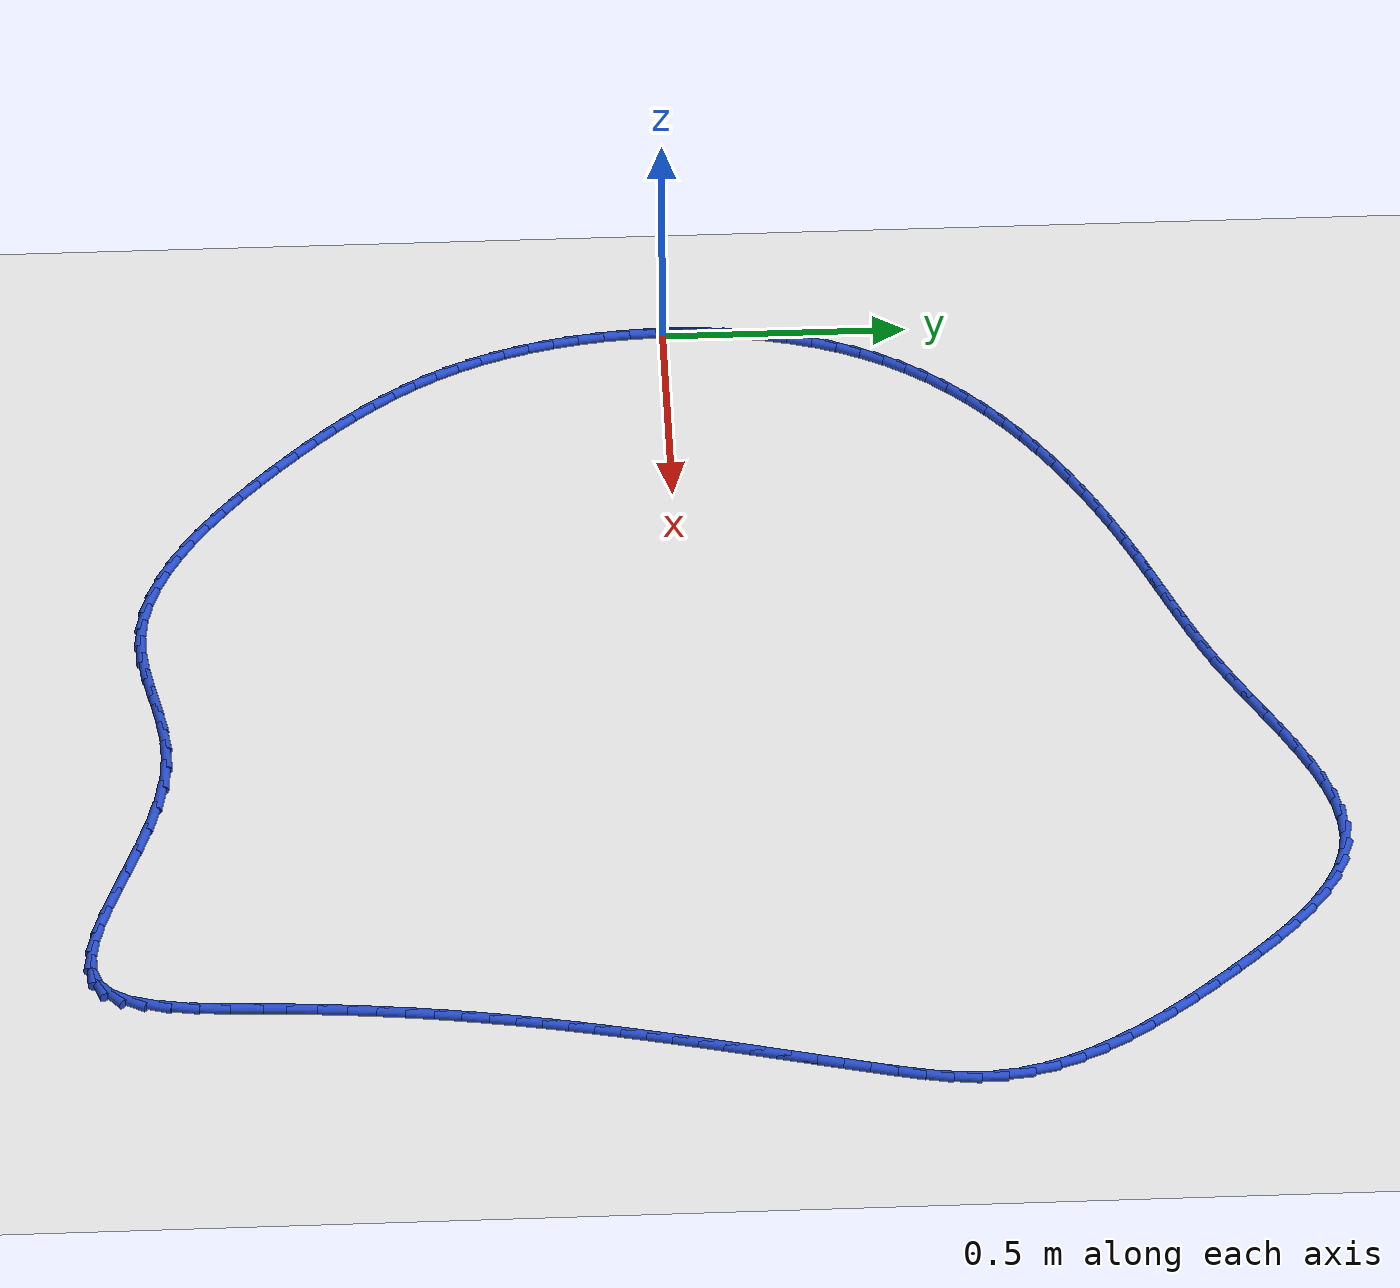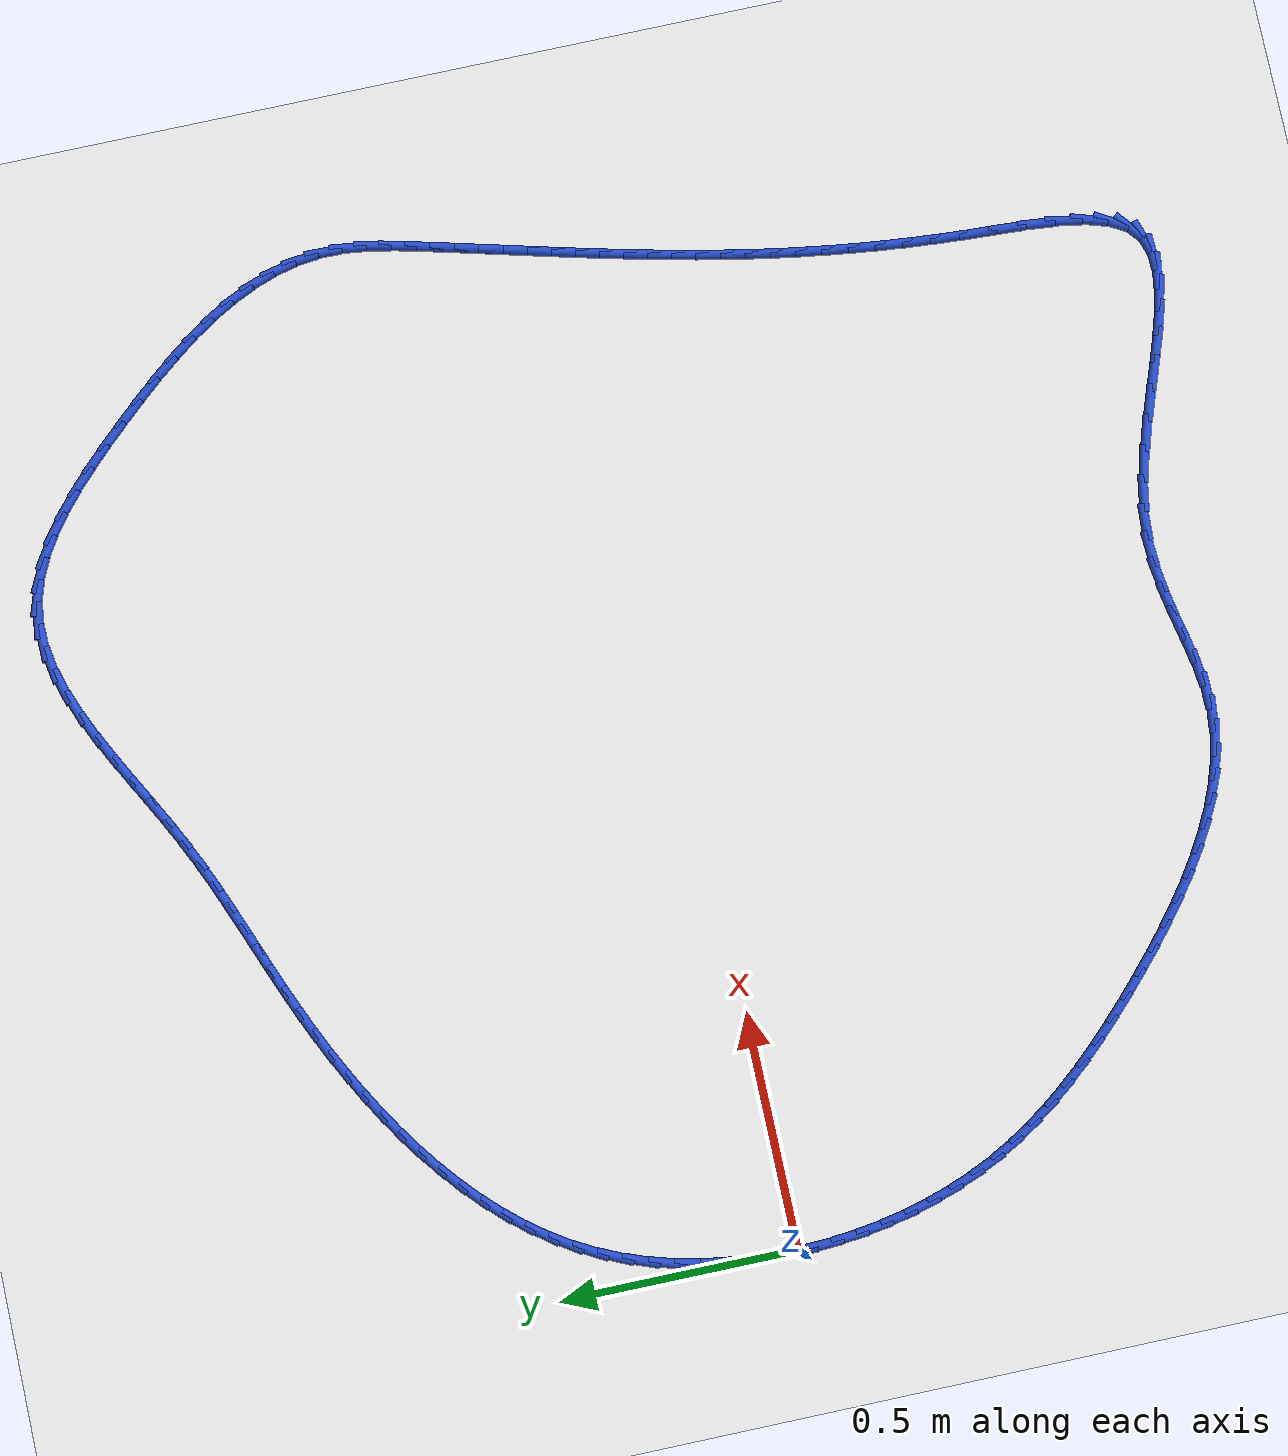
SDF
<sdf version="1.6">
 <world name="default">
  <light name="sun" type="directional">
   <pose>0 0 10 0 -0 0</pose>
   <diffuse>0.8 0.8 0.8 1</diffuse>
   <specular>0.2 0.2 0.2 1</specular>
   <attenuation>
    <range>1000</range>
    <constant>0.9</constant>
    <linear>0.01</linear>
    <quadratic>0.001</quadratic>
   </attenuation>
   <direction>-0.5 0.1 -0.9</direction>
  </light>
  <model name="ground_plane">
   <static>1</static>
   <link name="link">
    <collision name="collision">
     <geometry><plane><normal>0 0 1</normal><size>100 100</size></plane></geometry>
     <surface><friction><ode><mu>100</mu><mu2>50</mu2></ode></friction></surface>
    </collision>
    <visual name="visual">
     <cast_shadows>0</cast_shadows>
     <geometry><plane><normal>0 0 1</normal><size>100 100</size></plane></geometry>
     <material>
      <script><uri>file://media/materials/scripts/gazebo.material</uri><name>Gazebo/WhiteGlow</name></script>
     </material>
    </visual>
   </link>
  </model>
  <gravity>0 0 -9.8</gravity>
  <magnetic_field>6e-06 2.3e-05 -4.2e-05</magnetic_field>
  <atmosphere type="adiabatic"/>
  <physics name="default_physics" default="0" type="ode">
   <max_step_size>0.001</max_step_size>
   <real_time_factor>1</real_time_factor>
   <real_time_update_rate>1000</real_time_update_rate>
  </physics>
  <scene><ambient>0.4 0.4 0.4 1</ambient><background>0.7 0.7 0.7 1</background><shadows>1</shadows></scene>
  <spherical_coordinates>
   <surface_model>EARTH_WGS84</surface_model>
   <latitude_deg>0</latitude_deg>
   <longitude_deg>0</longitude_deg>
   <elevation>0</elevation>
   <heading_deg>0</heading_deg>
  </spherical_coordinates>
  <model name="line">
   <link name="link_0">
    <pose>2.42861286636753e-17 1.5265566588595902e-16 0.01 0 1.57 1.5557548040835374</pose>
    <collision name="collision">
     <geometry><cylinder><radius>0.01</radius><length>0.08</length></cylinder></geometry>
    </collision>
    <visual name="visual">
     <material>
      <script><name>Gazebo/Blue</name><uri>file://media/materials/scripts/gazebo.material</uri></script>
     </material>
     <geometry><cylinder><radius>0.01</radius><length>0.08</length></cylinder></geometry>
    </visual>
   </link>
   <link name="link_1">
    <pose>0.0008200648605110411 0.05451595755726912 0.01 0 1.57 1.5050673711794076</pose>
    <collision name="collision">
     <geometry><cylinder><radius>0.01</radius><length>0.08</length></cylinder></geometry>
    </collision>
    <visual name="visual">
     <material>
      <script><name>Gazebo/Blue</name><uri>file://media/materials/scripts/gazebo.material</uri></script>
     </material>
     <geometry><cylinder><radius>0.01</radius><length>0.08</length></cylinder></geometry>
    </visual>
   </link>
   <link name="link_2">
    <pose>0.004396346790956089 0.10884711518278226 0.01 0 1.57 1.4518409554157006</pose>
    <collision name="collision">
     <geometry><cylinder><radius>0.01</radius><length>0.08</length></cylinder></geometry>
    </collision>
    <visual name="visual">
     <material>
      <script><name>Gazebo/Blue</name><uri>file://media/materials/scripts/gazebo.material</uri></script>
     </material>
     <geometry><cylinder><radius>0.01</radius><length>0.08</length></cylinder></geometry>
    </visual>
   </link>
   <link name="link_3">
    <pose>0.010837198205843404 0.16273659051005376 0.01 0 1.57 1.3956293065094485</pose>
    <collision name="collision">
     <geometry><cylinder><radius>0.01</radius><length>0.08</length></cylinder></geometry>
    </collision>
    <visual name="visual">
     <material>
      <script><name>Gazebo/Blue</name><uri>file://media/materials/scripts/gazebo.material</uri></script>
     </material>
     <geometry><cylinder><radius>0.01</radius><length>0.08</length></cylinder></geometry>
    </visual>
   </link>
   <link name="link_4">
    <pose>0.020250971519681284 0.21592750117259812 0.01 0 1.57 1.3360020327878124</pose>
    <collision name="collision">
     <geometry><cylinder><radius>0.01</radius><length>0.08</length></cylinder></geometry>
    </collision>
    <visual name="visual">
     <material>
      <script><name>Gazebo/Blue</name><uri>file://media/materials/scripts/gazebo.material</uri></script>
     </material>
     <geometry><cylinder><radius>0.01</radius><length>0.08</length></cylinder></geometry>
    </visual>
   </link>
   <link name="link_5">
    <pose>0.03274601914697797 0.26816296480392954 0.01 0 1.57 1.2725615272935986</pose>
    <collision name="collision">
     <geometry><cylinder><radius>0.01</radius><length>0.08</length></cylinder></geometry>
    </collision>
    <visual name="visual">
     <material>
      <script><name>Gazebo/Blue</name><uri>file://media/materials/scripts/gazebo.material</uri></script>
     </material>
     <geometry><cylinder><radius>0.01</radius><length>0.08</length></cylinder></geometry>
    </visual>
   </link>
   <link name="link_6">
    <pose>0.04843069350224178 0.31918609903756245 0.01 0 1.57 1.204968856224903</pose>
    <collision name="collision">
     <geometry><cylinder><radius>0.01</radius><length>0.08</length></cylinder></geometry>
    </collision>
    <visual name="visual">
     <material>
      <script><name>Gazebo/Blue</name><uri>file://media/materials/scripts/gazebo.material</uri></script>
     </material>
     <geometry><cylinder><radius>0.01</radius><length>0.08</length></cylinder></geometry>
    </visual>
   </link>
   <link name="link_7">
    <pose>0.06741334699998093 0.36874002150701113 0.01 0 1.57 1.1329794530025175</pose>
    <collision name="collision">
     <geometry><cylinder><radius>0.01</radius><length>0.08</length></cylinder></geometry>
    </collision>
    <visual name="visual">
     <material>
      <script><name>Gazebo/Blue</name><uri>file://media/materials/scripts/gazebo.material</uri></script>
     </material>
     <geometry><cylinder><radius>0.01</radius><length>0.08</length></cylinder></geometry>
    </visual>
   </link>
   <link name="link_8">
    <pose>0.08980233205470373 0.4165678498457899 0.01 0 1.57 1.0568599665323917</pose>
    <collision name="collision">
     <geometry><cylinder><radius>0.01</radius><length>0.08</length></cylinder></geometry>
    </collision>
    <visual name="visual">
     <material>
      <script><name>Gazebo/Blue</name><uri>file://media/materials/scripts/gazebo.material</uri></script>
     </material>
     <geometry><cylinder><radius>0.01</radius><length>0.08</length></cylinder></geometry>
    </visual>
   </link>
   <link name="link_9">
    <pose>0.11569056184922914 0.4624252130635277 0.01 0 1.57 0.9817550211952442</pose>
    <collision name="collision">
     <geometry><cylinder><radius>0.01</radius><length>0.08</length></cylinder></geometry>
    </collision>
    <visual name="visual">
     <material>
      <script><name>Gazebo/Blue</name><uri>file://media/materials/scripts/gazebo.material</uri></script>
     </material>
     <geometry><cylinder><radius>0.01</radius><length>0.08</length></cylinder></geometry>
    </visual>
   </link>
   <link name="link_10">
    <pose>0.14496345431723184 0.5062358865618725 0.01 0 1.57 0.9115878039380247</pose>
    <collision name="collision">
     <geometry><cylinder><radius>0.01</radius><length>0.08</length></cylinder></geometry>
    </collision>
    <visual name="visual">
     <material>
      <script><name>Gazebo/Blue</name><uri>file://media/materials/scripts/gazebo.material</uri></script>
     </material>
     <geometry><cylinder><radius>0.01</radius><length>0.08</length></cylinder></geometry>
    </visual>
   </link>
   <link name="link_11">
    <pose>0.17735793236877923 0.5480439805576308 0.01 0 1.57 0.8466045933925027</pose>
    <collision name="collision">
     <geometry><cylinder><radius>0.01</radius><length>0.08</length></cylinder></geometry>
    </collision>
    <visual name="visual">
     <material>
      <script><name>Gazebo/Blue</name><uri>file://media/materials/scripts/gazebo.material</uri></script>
     </material>
     <geometry><cylinder><radius>0.01</radius><length>0.08</length></cylinder></geometry>
    </visual>
   </link>
   <link name="link_12">
    <pose>0.21260769531818516 0.5878962175490843 0.01 0 1.57 0.7867752115742281</pose>
    <collision name="collision">
     <geometry><cylinder><radius>0.01</radius><length>0.08</length></cylinder></geometry>
    </collision>
    <visual name="visual">
     <material>
      <script><name>Gazebo/Blue</name><uri>file://media/materials/scripts/gazebo.material</uri></script>
     </material>
     <geometry><cylinder><radius>0.01</radius><length>0.08</length></cylinder></geometry>
    </visual>
   </link>
   <link name="link_13">
    <pose>0.2504464424797634 0.6258393200345136 0.01 0 1.57 0.7319257513694877</pose>
    <collision name="collision">
     <geometry><cylinder><radius>0.01</radius><length>0.08</length></cylinder></geometry>
    </collision>
    <visual name="visual">
     <material>
      <script><name>Gazebo/Blue</name><uri>file://media/materials/scripts/gazebo.material</uri></script>
     </material>
     <geometry><cylinder><radius>0.01</radius><length>0.08</length></cylinder></geometry>
    </visual>
   </link>
   <link name="link_14">
    <pose>0.29060787316782766 0.6619200105121996 0.01 0 1.57 0.6817888142367023</pose>
    <collision name="collision">
     <geometry><cylinder><radius>0.01</radius><length>0.08</length></cylinder></geometry>
    </collision>
    <visual name="visual">
     <material>
      <script><name>Gazebo/Blue</name><uri>file://media/materials/scripts/gazebo.material</uri></script>
     </material>
     <geometry><cylinder><radius>0.01</radius><length>0.08</length></cylinder></geometry>
    </visual>
   </link>
   <link name="link_15">
    <pose>0.332825686696692 0.6961850114804236 0.01 0 1.57 0.6360445579904854</pose>
    <collision name="collision">
     <geometry><cylinder><radius>0.01</radius><length>0.08</length></cylinder></geometry>
    </collision>
    <visual name="visual">
     <material>
      <script><name>Gazebo/Blue</name><uri>file://media/materials/scripts/gazebo.material</uri></script>
     </material>
     <geometry><cylinder><radius>0.01</radius><length>0.08</length></cylinder></geometry>
    </visual>
   </link>
   <link name="link_16">
    <pose>0.3768335823806701 0.7286810454374665 0.01 0 1.57 0.5943515515108755</pose>
    <collision name="collision">
     <geometry><cylinder><radius>0.01</radius><length>0.08</length></cylinder></geometry>
    </collision>
    <visual name="visual">
     <material>
      <script><name>Gazebo/Blue</name><uri>file://media/materials/scripts/gazebo.material</uri></script>
     </material>
     <geometry><cylinder><radius>0.01</radius><length>0.08</length></cylinder></geometry>
    </visual>
   </link>
   <link name="link_17">
    <pose>0.4223652595340758 0.7594548348816091 0.01 0 1.57 0.5563683840970425</pose>
    <collision name="collision">
     <geometry><cylinder><radius>0.01</radius><length>0.08</length></cylinder></geometry>
    </collision>
    <visual name="visual">
     <material>
      <script><name>Gazebo/Blue</name><uri>file://media/materials/scripts/gazebo.material</uri></script>
     </material>
     <geometry><cylinder><radius>0.01</radius><length>0.08</length></cylinder></geometry>
    </visual>
   </link>
   <link name="link_18">
    <pose>0.469154417471223 0.7885531023111331 0.01 0 1.57 0.5217678002501723</pose>
    <collision name="collision">
     <geometry><cylinder><radius>0.01</radius><length>0.08</length></cylinder></geometry>
    </collision>
    <visual name="visual">
     <material>
      <script><name>Gazebo/Blue</name><uri>file://media/materials/scripts/gazebo.material</uri></script>
     </material>
     <geometry><cylinder><radius>0.01</radius><length>0.08</length></cylinder></geometry>
    </visual>
   </link>
   <link name="link_19">
    <pose>0.5169347555064254 0.8160225702243189 0.01 0 1.57 0.4902452585843131</pose>
    <collision name="collision">
     <geometry><cylinder><radius>0.01</radius><length>0.08</length></cylinder></geometry>
    </collision>
    <visual name="visual">
     <material>
      <script><name>Gazebo/Blue</name><uri>file://media/materials/scripts/gazebo.material</uri></script>
     </material>
     <geometry><cylinder><radius>0.01</radius><length>0.08</length></cylinder></geometry>
    </visual>
   </link>
   <link name="link_20">
    <pose>0.5654399729539971 0.8419099611194478 0.01 0 1.57 0.4615235999922261</pose>
    <collision name="collision">
     <geometry><cylinder><radius>0.01</radius><length>0.08</length></cylinder></geometry>
    </collision>
    <visual name="visual">
     <material>
      <script><name>Gazebo/Blue</name><uri>file://media/materials/scripts/gazebo.material</uri></script>
     </material>
     <geometry><cylinder><radius>0.01</radius><length>0.08</length></cylinder></geometry>
    </visual>
   </link>
   <link name="link_21">
    <pose>0.6144037691282513 0.8662619974948006 0.01 0 1.57 0.4353551821730655</pose>
    <collision name="collision">
     <geometry><cylinder><radius>0.01</radius><length>0.08</length></cylinder></geometry>
    </collision>
    <visual name="visual">
     <material>
      <script><name>Gazebo/Blue</name><uri>file://media/materials/scripts/gazebo.material</uri></script>
     </material>
     <geometry><cylinder><radius>0.01</radius><length>0.08</length></cylinder></geometry>
    </visual>
   </link>
   <link name="link_22">
    <pose>0.6635598433435026 0.8891254018486585 0.01 0 1.57 0.41154979110121537</pose>
    <collision name="collision">
     <geometry><cylinder><radius>0.01</radius><length>0.08</length></cylinder></geometry>
    </collision>
    <visual name="visual">
     <material>
      <script><name>Gazebo/Blue</name><uri>file://media/materials/scripts/gazebo.material</uri></script>
     </material>
     <geometry><cylinder><radius>0.01</radius><length>0.08</length></cylinder></geometry>
    </visual>
   </link>
   <link name="link_23">
    <pose>0.7126441373887852 0.9105494691565788 0.01 0 1.57 0.39162564742065387</pose>
    <collision name="collision">
     <geometry><cylinder><radius>0.01</radius><length>0.08</length></cylinder></geometry>
    </collision>
    <visual name="visual">
     <material>
      <script><name>Gazebo/Blue</name><uri>file://media/materials/scripts/gazebo.material</uri></script>
     </material>
     <geometry><cylinder><radius>0.01</radius><length>0.08</length></cylinder></geometry>
    </visual>
   </link>
   <link name="link_24">
    <pose>0.7615246641967388 0.9307350011257711 0.01 0 1.57 0.37841411007136366</pose>
    <collision name="collision">
     <geometry><cylinder><radius>0.01</radius><length>0.08</length></cylinder></geometry>
    </collision>
    <visual name="visual">
     <material>
      <script><name>Gazebo/Blue</name><uri>file://media/materials/scripts/gazebo.material</uri></script>
     </material>
     <geometry><cylinder><radius>0.01</radius><length>0.08</length></cylinder></geometry>
    </visual>
   </link>
   <link name="link_25">
    <pose>0.8102727350679035 0.9501160152169417 0.01 0 1.57 0.37249266737449443</pose>
    <collision name="collision">
     <geometry><cylinder><radius>0.01</radius><length>0.08</length></cylinder></geometry>
    </collision>
    <visual name="visual">
     <material>
      <script><name>Gazebo/Blue</name><uri>file://media/materials/scripts/gazebo.material</uri></script>
     </material>
     <geometry><cylinder><radius>0.01</radius><length>0.08</length></cylinder></geometry>
    </visual>
   </link>
   <link name="link_26">
    <pose>0.8589769853498858 0.9691464023444392 0.01 0 1.57 0.3740178413786772</pose>
    <collision name="collision">
     <geometry><cylinder><radius>0.01</radius><length>0.08</length></cylinder></geometry>
    </collision>
    <visual name="visual">
     <material>
      <script><name>Gazebo/Blue</name><uri>file://media/materials/scripts/gazebo.material</uri></script>
     </material>
     <geometry><cylinder><radius>0.01</radius><length>0.08</length></cylinder></geometry>
    </visual>
   </link>
   <link name="link_27">
    <pose>0.9077260503902914 0.9882800534226118 0.01 0 1.57 0.3829341860649818</pose>
    <collision name="collision">
     <geometry><cylinder><radius>0.01</radius><length>0.08</length></cylinder></geometry>
    </collision>
    <visual name="visual">
     <material>
      <script><name>Gazebo/Blue</name><uri>file://media/materials/scripts/gazebo.material</uri></script>
     </material>
     <geometry><cylinder><radius>0.01</radius><length>0.08</length></cylinder></geometry>
    </visual>
   </link>
   <link name="link_28">
    <pose>0.956608565536727 1.007970859365809 0.01 0 1.57 0.39897609293077424</pose>
    <collision name="collision">
     <geometry><cylinder><radius>0.01</radius><length>0.08</length></cylinder></geometry>
    </collision>
    <visual name="visual">
     <material>
      <script><name>Gazebo/Blue</name><uri>file://media/materials/scripts/gazebo.material</uri></script>
     </material>
     <geometry><cylinder><radius>0.01</radius><length>0.08</length></cylinder></geometry>
    </visual>
   </link>
   <link name="link_29">
    <pose>1.0057131661367986 1.0286727110883789 0.01 0 1.57 0.4216734961333918</pose>
    <collision name="collision">
     <geometry><cylinder><radius>0.01</radius><length>0.08</length></cylinder></geometry>
    </collision>
    <visual name="visual">
     <material>
      <script><name>Gazebo/Blue</name><uri>file://media/materials/scripts/gazebo.material</uri></script>
     </material>
     <geometry><cylinder><radius>0.01</radius><length>0.08</length></cylinder></geometry>
    </visual>
   </link>
   <link name="link_30">
    <pose>1.0551284875381124 1.0508394995046701 0.01 0 1.57 0.4503636769735263</pose>
    <collision name="collision">
     <geometry><cylinder><radius>0.01</radius><length>0.08</length></cylinder></geometry>
    </collision>
    <visual name="visual">
     <material>
      <script><name>Gazebo/Blue</name><uri>file://media/materials/scripts/gazebo.material</uri></script>
     </material>
     <geometry><cylinder><radius>0.01</radius><length>0.08</length></cylinder></geometry>
    </visual>
   </link>
   <link name="link_31">
    <pose>1.1049431589496737 1.0749250765799137 0.01 0 1.57 0.4800818102077247</pose>
    <collision name="collision">
     <geometry><cylinder><radius>0.01</radius><length>0.08</length></cylinder></geometry>
    </collision>
    <visual name="visual">
     <material>
      <script><name>Gazebo/Blue</name><uri>file://media/materials/scripts/gazebo.material</uri></script>
     </material>
     <geometry><cylinder><radius>0.01</radius><length>0.08</length></cylinder></geometry>
    </visual>
   </link>
   <link name="link_32">
    <pose>1.1552003304086138 1.1010947311885868 0.01 0 1.57 0.496960831944077</pose>
    <collision name="collision">
     <geometry><cylinder><radius>0.01</radius><length>0.08</length></cylinder></geometry>
    </collision>
    <visual name="visual">
     <material>
      <script><name>Gazebo/Blue</name><uri>file://media/materials/scripts/gazebo.material</uri></script>
     </material>
     <geometry><cylinder><radius>0.01</radius><length>0.08</length></cylinder></geometry>
    </visual>
   </link>
   <link name="link_33">
    <pose>1.2057883932143312 1.1285318156869555 0.01 0 1.57 0.49910432871639004</pose>
    <collision name="collision">
     <geometry><cylinder><radius>0.01</radius><length>0.08</length></cylinder></geometry>
    </collision>
    <visual name="visual">
     <material>
      <script><name>Gazebo/Blue</name><uri>file://media/materials/scripts/gazebo.material</uri></script>
     </material>
     <geometry><cylinder><radius>0.01</radius><length>0.08</length></cylinder></geometry>
    </visual>
   </link>
   <link name="link_34">
    <pose>1.256562850258894 1.1562110071173273 0.01 0 1.57 0.48679470036189326</pose>
    <collision name="collision">
     <geometry><cylinder><radius>0.01</radius><length>0.08</length></cylinder></geometry>
    </collision>
    <visual name="visual">
     <material>
      <script><name>Gazebo/Blue</name><uri>file://media/materials/scripts/gazebo.material</uri></script>
     </material>
     <geometry><cylinder><radius>0.01</radius><length>0.08</length></cylinder></geometry>
    </visual>
   </link>
   <link name="link_35">
    <pose>1.3073792044343693 1.1831069825220106 0.01 0 1.57 0.4593882063054732</pose>
    <collision name="collision">
     <geometry><cylinder><radius>0.01</radius><length>0.08</length></cylinder></geometry>
    </collision>
    <visual name="visual">
     <material>
      <script><name>Gazebo/Blue</name><uri>file://media/materials/scripts/gazebo.material</uri></script>
     </material>
     <geometry><cylinder><radius>0.01</radius><length>0.08</length></cylinder></geometry>
    </visual>
   </link>
   <link name="link_36">
    <pose>1.3580929586328243 1.2081944189433134 0.01 0 1.57 0.41530751775124203</pose>
    <collision name="collision">
     <geometry><cylinder><radius>0.01</radius><length>0.08</length></cylinder></geometry>
    </collision>
    <visual name="visual">
     <material>
      <script><name>Gazebo/Blue</name><uri>file://media/materials/scripts/gazebo.material</uri></script>
     </material>
     <geometry><cylinder><radius>0.01</radius><length>0.08</length></cylinder></geometry>
    </visual>
   </link>
   <link name="link_37">
    <pose>1.4085596157463276 1.2304479934235437 0.01 0 1.57 0.35203496237146453</pose>
    <collision name="collision">
     <geometry><cylinder><radius>0.01</radius><length>0.08</length></cylinder></geometry>
    </collision>
    <visual name="visual">
     <material>
      <script><name>Gazebo/Blue</name><uri>file://media/materials/scripts/gazebo.material</uri></script>
     </material>
     <geometry><cylinder><radius>0.01</radius><length>0.08</length></cylinder></geometry>
    </visual>
   </link>
   <link name="link_38">
    <pose>1.4586346786669466 1.2488423830050095 0.01 0 1.57 0.26623801589896795</pose>
    <collision name="collision">
     <geometry><cylinder><radius>0.01</radius><length>0.08</length></cylinder></geometry>
    </collision>
    <visual name="visual">
     <material>
      <script><name>Gazebo/Blue</name><uri>file://media/materials/scripts/gazebo.material</uri></script>
     </material>
     <geometry><cylinder><radius>0.01</radius><length>0.08</length></cylinder></geometry>
    </visual>
   </link>
   <link name="link_39">
    <pose>1.5081736502867489 1.2623522647300194 0.01 0 1.57 0.15431593757000223</pose>
    <collision name="collision">
     <geometry><cylinder><radius>0.01</radius><length>0.08</length></cylinder></geometry>
    </collision>
    <visual name="visual">
     <material>
      <script><name>Gazebo/Blue</name><uri>file://media/materials/scripts/gazebo.material</uri></script>
     </material>
     <geometry><cylinder><radius>0.01</radius><length>0.08</length></cylinder></geometry>
    </visual>
   </link>
   <link name="link_40">
    <pose>1.5570320334978012 1.2699523156408798 0.01 0 1.57 0.013841537188865709</pose>
    <collision name="collision">
     <geometry><cylinder><radius>0.01</radius><length>0.08</length></cylinder></geometry>
    </collision>
    <visual name="visual">
     <material>
      <script><name>Gazebo/Blue</name><uri>file://media/materials/scripts/gazebo.material</uri></script>
     </material>
     <geometry><cylinder><radius>0.01</radius><length>0.08</length></cylinder></geometry>
    </visual>
   </link>
   <link name="link_41">
    <pose>1.6050653311921725 1.2706172127799007 0.01 0 1.57 -0.1530114130559788</pose>
    <collision name="collision">
     <geometry><cylinder><radius>0.01</radius><length>0.08</length></cylinder></geometry>
    </collision>
    <visual name="visual">
     <material>
      <script><name>Gazebo/Blue</name><uri>file://media/materials/scripts/gazebo.material</uri></script>
     </material>
     <geometry><cylinder><radius>0.01</radius><length>0.08</length></cylinder></geometry>
    </visual>
   </link>
   <link name="link_42">
    <pose>1.6521323606039902 1.2633586847430738 0.01 0 1.57 -0.3194102189316025</pose>
    <collision name="collision">
     <geometry><cylinder><radius>0.01</radius><length>0.08</length></cylinder></geometry>
    </collision>
    <visual name="visual">
     <material>
      <script><name>Gazebo/Blue</name><uri>file://media/materials/scripts/gazebo.material</uri></script>
     </material>
     <geometry><cylinder><radius>0.01</radius><length>0.08</length></cylinder></geometry>
    </visual>
   </link>
   <link name="link_43">
    <pose>1.698176195550206 1.2481303777815838 0.01 0 1.57 -0.4587249353660347</pose>
    <collision name="collision">
     <geometry><cylinder><radius>0.01</radius><length>0.08</length></cylinder></geometry>
    </collision>
    <visual name="visual">
     <material>
      <script><name>Gazebo/Blue</name><uri>file://media/materials/scripts/gazebo.material</uri></script>
     </material>
     <geometry><cylinder><radius>0.01</radius><length>0.08</length></cylinder></geometry>
    </visual>
   </link>
   <link name="link_44">
    <pose>1.7432288827547004 1.2258805803342752 0.01 0 1.57 -0.570161706124903</pose>
    <collision name="collision">
     <geometry><cylinder><radius>0.01</radius><length>0.08</length></cylinder></geometry>
    </collision>
    <visual name="visual">
     <material>
      <script><name>Gazebo/Blue</name><uri>file://media/materials/scripts/gazebo.material</uri></script>
     </material>
     <geometry><cylinder><radius>0.01</radius><length>0.08</length></cylinder></geometry>
    </visual>
   </link>
   <link name="link_45">
    <pose>1.7873267274254852 1.1976051871071476 0.01 0 1.57 -0.6570073161786348</pose>
    <collision name="collision">
     <geometry><cylinder><radius>0.01</radius><length>0.08</length></cylinder></geometry>
    </collision>
    <visual name="visual">
     <material>
      <script><name>Gazebo/Blue</name><uri>file://media/materials/scripts/gazebo.material</uri></script>
     </material>
     <geometry><cylinder><radius>0.01</radius><length>0.08</length></cylinder></geometry>
    </visual>
   </link>
   <link name="link_46">
    <pose>1.8305060347705737 1.1643000928061977 0.01 0 1.57 -0.7232179390403781</pose>
    <collision name="collision">
     <geometry><cylinder><radius>0.01</radius><length>0.08</length></cylinder></geometry>
    </collision>
    <visual name="visual">
     <material>
      <script><name>Gazebo/Blue</name><uri>file://media/materials/scripts/gazebo.material</uri></script>
     </material>
     <geometry><cylinder><radius>0.01</radius><length>0.08</length></cylinder></geometry>
    </visual>
   </link>
   <link name="link_47">
    <pose>1.8728031099979794 1.1269611921374258 0.01 0 1.57 -0.7722697137196393</pose>
    <collision name="collision">
     <geometry><cylinder><radius>0.01</radius><length>0.08</length></cylinder></geometry>
    </collision>
    <visual name="visual">
     <material>
      <script><name>Gazebo/Blue</name><uri>file://media/materials/scripts/gazebo.material</uri></script>
     </material>
     <geometry><cylinder><radius>0.01</radius><length>0.08</length></cylinder></geometry>
    </visual>
   </link>
   <link name="link_48">
    <pose>1.9142542583157152 1.0865843798068282 0.01 0 1.57 -0.8067926237513624</pose>
    <collision name="collision">
     <geometry><cylinder><radius>0.01</radius><length>0.08</length></cylinder></geometry>
    </collision>
    <visual name="visual">
     <material>
      <script><name>Gazebo/Blue</name><uri>file://media/materials/scripts/gazebo.material</uri></script>
     </material>
     <geometry><cylinder><radius>0.01</radius><length>0.08</length></cylinder></geometry>
    </visual>
   </link>
   <link name="link_49">
    <pose>1.9548957849317943 1.044165550520405 0.01 0 1.57 -0.8286929260010305</pose>
    <collision name="collision">
     <geometry><cylinder><radius>0.01</radius><length>0.08</length></cylinder></geometry>
    </collision>
    <visual name="visual">
     <material>
      <script><name>Gazebo/Blue</name><uri>file://media/materials/scripts/gazebo.material</uri></script>
     </material>
     <geometry><cylinder><radius>0.01</radius><length>0.08</length></cylinder></geometry>
    </visual>
   </link>
   <link name="link_50">
    <pose>1.9947591201268489 1.0006919044576394 0.01 0 1.57 -0.8465490979296157</pose>
    <collision name="collision">
     <geometry><cylinder><radius>0.01</radius><length>0.08</length></cylinder></geometry>
    </collision>
    <visual name="visual">
     <material>
      <script><name>Gazebo/Blue</name><uri>file://media/materials/scripts/gazebo.material</uri></script>
     </material>
     <geometry><cylinder><radius>0.01</radius><length>0.08</length></cylinder></geometry>
    </visual>
   </link>
   <link name="link_51">
    <pose>2.033643117156977 0.9567358362126579 0.01 0 1.57 -0.8717102694216153</pose>
    <collision name="collision">
     <geometry><cylinder><radius>0.01</radius><length>0.08</length></cylinder></geometry>
    </collision>
    <visual name="visual">
     <material>
      <script><name>Gazebo/Blue</name><uri>file://media/materials/scripts/gazebo.material</uri></script>
     </material>
     <geometry><cylinder><radius>0.01</radius><length>0.08</length></cylinder></geometry>
    </visual>
   </link>
   <link name="link_52">
    <pose>2.0710169210331135 0.9122816993987162 0.01 0 1.57 -0.9056417686828994</pose>
    <collision name="collision">
     <geometry><cylinder><radius>0.01</radius><length>0.08</length></cylinder></geometry>
    </collision>
    <visual name="visual">
     <material>
      <script><name>Gazebo/Blue</name><uri>file://media/materials/scripts/gazebo.material</uri></script>
     </material>
     <geometry><cylinder><radius>0.01</radius><length>0.08</length></cylinder></geometry>
    </visual>
   </link>
   <link name="link_53">
    <pose>2.106324630868863 0.8672691777906644 0.01 0 1.57 -0.9492133114182162</pose>
    <collision name="collision">
     <geometry><cylinder><radius>0.01</radius><length>0.08</length></cylinder></geometry>
    </collision>
    <visual name="visual">
     <material>
      <script><name>Gazebo/Blue</name><uri>file://media/materials/scripts/gazebo.material</uri></script>
     </material>
     <geometry><cylinder><radius>0.01</radius><length>0.08</length></cylinder></geometry>
    </visual>
   </link>
   <link name="link_54">
    <pose>2.139010345777828 0.8216379551633507 0.01 0 1.57 -1.003488408451562</pose>
    <collision name="collision">
     <geometry><cylinder><radius>0.01</radius><length>0.08</length></cylinder></geometry>
    </collision>
    <visual name="visual">
     <material>
      <script><name>Gazebo/Blue</name><uri>file://media/materials/scripts/gazebo.material</uri></script>
     </material>
     <geometry><cylinder><radius>0.01</radius><length>0.08</length></cylinder></geometry>
    </visual>
   </link>
   <link name="link_55">
    <pose>2.168518164873613 0.7753277152916239 0.01 0 1.57 -1.0696393937264592</pose>
    <collision name="collision">
     <geometry><cylinder><radius>0.01</radius><length>0.08</length></cylinder></geometry>
    </collision>
    <visual name="visual">
     <material>
      <script><name>Gazebo/Blue</name><uri>file://media/materials/scripts/gazebo.material</uri></script>
     </material>
     <geometry><cylinder><radius>0.01</radius><length>0.08</length></cylinder></geometry>
    </visual>
   </link>
   <link name="link_56">
    <pose>2.194292187269821 0.728278141950333 0.01 0 1.57 -1.1487739009880455</pose>
    <collision name="collision">
     <geometry><cylinder><radius>0.01</radius><length>0.08</length></cylinder></geometry>
    </collision>
    <visual name="visual">
     <material>
      <script><name>Gazebo/Blue</name><uri>file://media/materials/scripts/gazebo.material</uri></script>
     </material>
     <geometry><cylinder><radius>0.01</radius><length>0.08</length></cylinder></geometry>
    </visual>
   </link>
   <link name="link_57">
    <pose>2.2157765120800557 0.6804289189143266 0.01 0 1.57 -1.241630429142435</pose>
    <collision name="collision">
     <geometry><cylinder><radius>0.01</radius><length>0.08</length></cylinder></geometry>
    </collision>
    <visual name="visual">
     <material>
      <script><name>Gazebo/Blue</name><uri>file://media/materials/scripts/gazebo.material</uri></script>
     </material>
     <geometry><cylinder><radius>0.01</radius><length>0.08</length></cylinder></geometry>
    </visual>
   </link>
   <link name="link_58">
    <pose>2.2324152384179214 0.631719729958454 0.01 0 1.57 -1.3481283788459681</pose>
    <collision name="collision">
     <geometry><cylinder><radius>0.01</radius><length>0.08</length></cylinder></geometry>
    </collision>
    <visual name="visual">
     <material>
      <script><name>Gazebo/Blue</name><uri>file://media/materials/scripts/gazebo.material</uri></script>
     </material>
     <geometry><cylinder><radius>0.01</radius><length>0.08</length></cylinder></geometry>
    </visual>
   </link>
   <link name="link_59">
    <pose>2.2436524653970213 0.5820902588575636 0.01 0 1.57 -1.4668486992127596</pose>
    <collision name="collision">
     <geometry><cylinder><radius>0.01</radius><length>0.08</length></cylinder></geometry>
    </collision>
    <visual name="visual">
     <material>
      <script><name>Gazebo/Blue</name><uri>file://media/materials/scripts/gazebo.material</uri></script>
     </material>
     <geometry><cylinder><radius>0.01</radius><length>0.08</length></cylinder></geometry>
    </visual>
   </link>
   <link name="link_60">
    <pose>2.248932292130959 0.5314801893865047 0.01 0 1.57 1.5481075125097459</pose>
    <collision name="collision">
     <geometry><cylinder><radius>0.01</radius><length>0.08</length></cylinder></geometry>
    </collision>
    <visual name="visual">
     <material>
      <script><name>Gazebo/Blue</name><uri>file://media/materials/scripts/gazebo.material</uri></script>
     </material>
     <geometry><cylinder><radius>0.01</radius><length>0.08</length></cylinder></geometry>
    </visual>
   </link>
   <link name="link_61">
    <pose>2.2477605343638296 0.4798443181246754 0.01 0 1.57 1.4399671318108693</pose>
    <collision name="collision">
     <geometry><cylinder><radius>0.01</radius><length>0.08</length></cylinder></geometry>
    </collision>
    <visual name="visual">
     <material>
      <script><name>Gazebo/Blue</name><uri>file://media/materials/scripts/gazebo.material</uri></script>
     </material>
     <geometry><cylinder><radius>0.01</radius><length>0.08</length></cylinder></geometry>
    </visual>
   </link>
   <link name="link_62">
    <pose>2.240864685935754 0.42743659897975306 0.01 0 1.57 1.3689984859225255</pose>
    <collision name="collision">
     <geometry><cylinder><radius>0.01</radius><length>0.08</length></cylinder></geometry>
    </collision>
    <visual name="visual">
     <material>
      <script><name>Gazebo/Blue</name><uri>file://media/materials/scripts/gazebo.material</uri></script>
     </material>
     <geometry><cylinder><radius>0.01</radius><length>0.08</length></cylinder></geometry>
    </visual>
   </link>
   <link name="link_63">
    <pose>2.2300931912438684 0.37478547762189884 0.01 0 1.57 1.331791199553235</pose>
    <collision name="collision">
     <geometry><cylinder><radius>0.01</radius><length>0.08</length></cylinder></geometry>
    </collision>
    <visual name="visual">
     <material>
      <script><name>Gazebo/Blue</name><uri>file://media/materials/scripts/gazebo.material</uri></script>
     </material>
     <geometry><cylinder><radius>0.01</radius><length>0.08</length></cylinder></geometry>
    </visual>
   </link>
   <link name="link_64">
    <pose>2.2173360190365723 0.32242956795955624 0.01 0 1.57 1.3218586392856893</pose>
    <collision name="collision">
     <geometry><cylinder><radius>0.01</radius><length>0.08</length></cylinder></geometry>
    </collision>
    <visual name="visual">
     <material>
      <script><name>Gazebo/Blue</name><uri>file://media/materials/scripts/gazebo.material</uri></script>
     </material>
     <geometry><cylinder><radius>0.01</radius><length>0.08</length></cylinder></geometry>
    </visual>
   </link>
   <link name="link_65">
    <pose>2.2042141581999113 0.2708115075608614 0.01 0 1.57 1.3188930635925054</pose>
    <collision name="collision">
     <geometry><cylinder><radius>0.01</radius><length>0.08</length></cylinder></geometry>
    </collision>
    <visual name="visual">
     <material>
      <script><name>Gazebo/Blue</name><uri>file://media/materials/scripts/gazebo.material</uri></script>
     </material>
     <geometry><cylinder><radius>0.01</radius><length>0.08</length></cylinder></geometry>
    </visual>
   </link>
   <link name="link_66">
    <pose>2.1911202199004194 0.21993562907030154 0.01 0 1.57 1.3172165367474906</pose>
    <collision name="collision">
     <geometry><cylinder><radius>0.01</radius><length>0.08</length></cylinder></geometry>
    </collision>
    <visual name="visual">
     <material>
      <script><name>Gazebo/Blue</name><uri>file://media/materials/scripts/gazebo.material</uri></script>
     </material>
     <geometry><cylinder><radius>0.01</radius><length>0.08</length></cylinder></geometry>
    </visual>
   </link>
   <link name="link_67">
    <pose>2.178096355582604 0.16968121546786363 0.01 0 1.57 1.3168856185074094</pose>
    <collision name="collision">
     <geometry><cylinder><radius>0.01</radius><length>0.08</length></cylinder></geometry>
    </collision>
    <visual name="visual">
     <material>
      <script><name>Gazebo/Blue</name><uri>file://media/materials/scripts/gazebo.material</uri></script>
     </material>
     <geometry><cylinder><radius>0.01</radius><length>0.08</length></cylinder></geometry>
    </visual>
   </link>
   <link name="link_68">
    <pose>2.165184690235538 0.11992754029380977 0.01 0 1.57 1.3179429791689798</pose>
    <collision name="collision">
     <geometry><cylinder><radius>0.01</radius><length>0.08</length></cylinder></geometry>
    </collision>
    <visual name="visual">
     <material>
      <script><name>Gazebo/Blue</name><uri>file://media/materials/scripts/gazebo.material</uri></script>
     </material>
     <geometry><cylinder><radius>0.01</radius><length>0.08</length></cylinder></geometry>
    </visual>
   </link>
   <link name="link_69">
    <pose>2.152427348848296 0.07055387708840355 0.01 0 1.57 1.3204153591134353</pose>
    <collision name="collision">
     <geometry><cylinder><radius>0.01</radius><length>0.08</length></cylinder></geometry>
    </collision>
    <visual name="visual">
     <material>
      <script><name>Gazebo/Blue</name><uri>file://media/materials/scripts/gazebo.material</uri></script>
     </material>
     <geometry><cylinder><radius>0.01</radius><length>0.08</length></cylinder></geometry>
    </visual>
   </link>
   <link name="link_70">
    <pose>2.139866456409954 0.021439499391907244 0.01 0 1.57 1.3243123006013406</pose>
    <collision name="collision">
     <geometry><cylinder><radius>0.01</radius><length>0.08</length></cylinder></geometry>
    </collision>
    <visual name="visual">
     <material>
      <script><name>Gazebo/Blue</name><uri>file://media/materials/scripts/gazebo.material</uri></script>
     </material>
     <geometry><cylinder><radius>0.01</radius><length>0.08</length></cylinder></geometry>
    </visual>
   </link>
   <link name="link_71">
    <pose>2.127544137909585 -0.02753631925541559 0.01 0 1.57 1.3296252855946606</pose>
    <collision name="collision">
     <geometry><cylinder><radius>0.01</radius><length>0.08</length></cylinder></geometry>
    </collision>
    <visual name="visual">
     <material>
      <script><name>Gazebo/Blue</name><uri>file://media/materials/scripts/gazebo.material</uri></script>
     </material>
     <geometry><cylinder><radius>0.01</radius><length>0.08</length></cylinder></geometry>
    </visual>
   </link>
   <link name="link_72">
    <pose>2.115502518336264 -0.07649430531330247 0.01 0 1.57 1.3363273409737746</pose>
    <collision name="collision">
     <geometry><cylinder><radius>0.01</radius><length>0.08</length></cylinder></geometry>
    </collision>
    <visual name="visual">
     <material>
      <script><name>Gazebo/Blue</name><uri>file://media/materials/scripts/gazebo.material</uri></script>
     </material>
     <geometry><cylinder><radius>0.01</radius><length>0.08</length></cylinder></geometry>
    </visual>
   </link>
   <link name="link_73">
    <pose>2.1037837226790645 -0.12555518524149126 0.01 0 1.57 1.344373157456931</pose>
    <collision name="collision">
     <geometry><cylinder><radius>0.01</radius><length>0.08</length></cylinder></geometry>
    </collision>
    <visual name="visual">
     <material>
      <script><name>Gazebo/Blue</name><uri>file://media/materials/scripts/gazebo.material</uri></script>
     </material>
     <geometry><cylinder><radius>0.01</radius><length>0.08</length></cylinder></geometry>
    </visual>
   </link>
   <link name="link_74">
    <pose>2.0924298759270634 -0.1748396854997176 0.01 0 1.57 1.3536997484083129</pose>
    <collision name="collision">
     <geometry><cylinder><radius>0.01</radius><length>0.08</length></cylinder></geometry>
    </collision>
    <visual name="visual">
     <material>
      <script><name>Gazebo/Blue</name><uri>file://media/materials/scripts/gazebo.material</uri></script>
     </material>
     <geometry><cylinder><radius>0.01</radius><length>0.08</length></cylinder></geometry>
    </visual>
   </link>
   <link name="link_75">
    <pose>2.081483103069332 -0.2244685325477193 0.01 0 1.57 1.364227649971051</pose>
    <collision name="collision">
     <geometry><cylinder><radius>0.01</radius><length>0.08</length></cylinder></geometry>
    </collision>
    <visual name="visual">
     <material>
      <script><name>Gazebo/Blue</name><uri>file://media/materials/scripts/gazebo.material</uri></script>
     </material>
     <geometry><cylinder><radius>0.01</radius><length>0.08</length></cylinder></geometry>
    </visual>
   </link>
   <link name="link_76">
    <pose>2.0709855290949477 -0.2745624528452336 0.01 0 1.57 1.3758626357622479</pose>
    <collision name="collision">
     <geometry><cylinder><radius>0.01</radius><length>0.08</length></cylinder></geometry>
    </collision>
    <visual name="visual">
     <material>
      <script><name>Gazebo/Blue</name><uri>file://media/materials/scripts/gazebo.material</uri></script>
     </material>
     <geometry><cylinder><radius>0.01</radius><length>0.08</length></cylinder></geometry>
    </visual>
   </link>
   <link name="link_77">
    <pose>2.0609792789929826 -0.32524217285199747 0.01 0 1.57 1.3884978897235525</pose>
    <collision name="collision">
     <geometry><cylinder><radius>0.01</radius><length>0.08</length></cylinder></geometry>
    </collision>
    <visual name="visual">
     <material>
      <script><name>Gazebo/Blue</name><uri>file://media/materials/scripts/gazebo.material</uri></script>
     </material>
     <geometry><cylinder><radius>0.01</radius><length>0.08</length></cylinder></geometry>
    </visual>
   </link>
   <link name="link_78">
    <pose>2.0515064777525125 -0.376628419027749 0.01 0 1.57 1.4020165523041561</pose>
    <collision name="collision">
     <geometry><cylinder><radius>0.01</radius><length>0.08</length></cylinder></geometry>
    </collision>
    <visual name="visual">
     <material>
      <script><name>Gazebo/Blue</name><uri>file://media/materials/scripts/gazebo.material</uri></script>
     </material>
     <geometry><cylinder><radius>0.01</radius><length>0.08</length></cylinder></geometry>
    </visual>
   </link>
   <link name="link_79">
    <pose>2.042609250362612 -0.4288419178322236 0.01 0 1.57 1.4162945310095587</pose>
    <collision name="collision">
     <geometry><cylinder><radius>0.01</radius><length>0.08</length></cylinder></geometry>
    </collision>
    <visual name="visual">
     <material>
      <script><name>Gazebo/Blue</name><uri>file://media/materials/scripts/gazebo.material</uri></script>
     </material>
     <geometry><cylinder><radius>0.01</radius><length>0.08</length></cylinder></geometry>
    </visual>
   </link>
   <link name="link_80">
    <pose>2.0343297218123544 -0.48200339572515927 0.01 0 1.57 1.4312034493797683</pose>
    <collision name="collision">
     <geometry><cylinder><radius>0.01</radius><length>0.08</length></cylinder></geometry>
    </collision>
    <visual name="visual">
     <material>
      <script><name>Gazebo/Blue</name><uri>file://media/materials/scripts/gazebo.material</uri></script>
     </material>
     <geometry><cylinder><radius>0.01</radius><length>0.08</length></cylinder></geometry>
    </visual>
   </link>
   <link name="link_81">
    <pose>2.026710017090815 -0.536233579166293 0.01 0 1.57 1.4466136009140425</pose>
    <collision name="collision">
     <geometry><cylinder><radius>0.01</radius><length>0.08</length></cylinder></geometry>
    </collision>
    <visual name="visual">
     <material>
      <script><name>Gazebo/Blue</name><uri>file://media/materials/scripts/gazebo.material</uri></script>
     </material>
     <geometry><cylinder><radius>0.01</radius><length>0.08</length></cylinder></geometry>
    </visual>
   </link>
   <link name="link_82">
    <pose>2.0197922611870682 -0.5916531946153631 0.01 0 1.57 1.4623967774550126</pose>
    <collision name="collision">
     <geometry><cylinder><radius>0.01</radius><length>0.08</length></cylinder></geometry>
    </collision>
    <visual name="visual">
     <material>
      <script><name>Gazebo/Blue</name><uri>file://media/materials/scripts/gazebo.material</uri></script>
     </material>
     <geometry><cylinder><radius>0.01</radius><length>0.08</length></cylinder></geometry>
    </visual>
   </link>
   <link name="link_83">
    <pose>2.0136185790901884 -0.6483829685321048 0.01 0 1.57 1.4784288548192208</pose>
    <collision name="collision">
     <geometry><cylinder><radius>0.01</radius><length>0.08</length></cylinder></geometry>
    </collision>
    <visual name="visual">
     <material>
      <script><name>Gazebo/Blue</name><uri>file://media/materials/scripts/gazebo.material</uri></script>
     </material>
     <geometry><cylinder><radius>0.01</radius><length>0.08</length></cylinder></geometry>
    </visual>
   </link>
   <link name="link_84">
    <pose>2.0082310957892493 -0.7065436273762558 0.01 0 1.57 1.4945920403894863</pose>
    <collision name="collision">
     <geometry><cylinder><radius>0.01</radius><length>0.08</length></cylinder></geometry>
    </collision>
    <visual name="visual">
     <material>
      <script><name>Gazebo/Blue</name><uri>file://media/materials/scripts/gazebo.material</uri></script>
     </material>
     <geometry><cylinder><radius>0.01</radius><length>0.08</length></cylinder></geometry>
    </visual>
   </link>
   <link name="link_85">
    <pose>2.003671936273327 -0.7662558976075535 0.01 0 1.57 1.5107702527589402</pose>
    <collision name="collision">
     <geometry><cylinder><radius>0.01</radius><length>0.08</length></cylinder></geometry>
    </collision>
    <visual name="visual">
     <material>
      <script><name>Gazebo/Blue</name><uri>file://media/materials/scripts/gazebo.material</uri></script>
     </material>
     <geometry><cylinder><radius>0.01</radius><length>0.08</length></cylinder></geometry>
    </visual>
   </link>
   <link name="link_86">
    <pose>1.9999828644491169 -0.8276398892168041 0.01 0 1.57 1.5211856129341004</pose>
    <collision name="collision">
     <geometry><cylinder><radius>0.01</radius><length>0.08</length></cylinder></geometry>
    </collision>
    <visual name="visual">
     <material>
      <script><name>Gazebo/Blue</name><uri>file://media/materials/scripts/gazebo.material</uri></script>
     </material>
     <geometry><cylinder><radius>0.01</radius><length>0.08</length></cylinder></geometry>
    </visual>
   </link>
   <link name="link_87">
    <pose>1.996874189954078 -0.8902498267571066 0.01 0 1.57 1.5099762439219886</pose>
    <collision name="collision">
     <geometry><cylinder><radius>0.01</radius><length>0.08</length></cylinder></geometry>
    </collision>
    <visual name="visual">
     <material>
      <script><name>Gazebo/Blue</name><uri>file://media/materials/scripts/gazebo.material</uri></script>
     </material>
     <geometry><cylinder><radius>0.01</radius><length>0.08</length></cylinder></geometry>
    </visual>
   </link>
   <link name="link_88">
    <pose>1.9931121845415385 -0.9520281972332748 0.01 0 1.57 1.4718778906153125</pose>
    <collision name="collision">
     <geometry><cylinder><radius>0.01</radius><length>0.08</length></cylinder></geometry>
    </collision>
    <visual name="visual">
     <material>
      <script><name>Gazebo/Blue</name><uri>file://media/materials/scripts/gazebo.material</uri></script>
     </material>
     <geometry><cylinder><radius>0.01</radius><length>0.08</length></cylinder></geometry>
    </visual>
   </link>
   <link name="link_89">
    <pose>1.9872961620909257 -1.010632443713991 0.01 0 1.57 1.3979088833808244</pose>
    <collision name="collision">
     <geometry><cylinder><radius>0.01</radius><length>0.08</length></cylinder></geometry>
    </collision>
    <visual name="visual">
     <material>
      <script><name>Gazebo/Blue</name><uri>file://media/materials/scripts/gazebo.material</uri></script>
     </material>
     <geometry><cylinder><radius>0.01</radius><length>0.08</length></cylinder></geometry>
    </visual>
   </link>
   <link name="link_90">
    <pose>1.9780254364816638 -1.0637200092679346 0.01 0 1.57 1.2680673224319479</pose>
    <collision name="collision">
     <geometry><cylinder><radius>0.01</radius><length>0.08</length></cylinder></geometry>
    </collision>
    <visual name="visual">
     <material>
      <script><name>Gazebo/Blue</name><uri>file://media/materials/scripts/gazebo.material</uri></script>
     </material>
     <geometry><cylinder><radius>0.01</radius><length>0.08</length></cylinder></geometry>
    </visual>
   </link>
   <link name="link_91">
    <pose>1.9638993215931781 -1.1089483369637878 0.01 0 1.57 1.0437866267493852</pose>
    <collision name="collision">
     <geometry><cylinder><radius>0.01</radius><length>0.08</length></cylinder></geometry>
    </collision>
    <visual name="visual">
     <material>
      <script><name>Gazebo/Blue</name><uri>file://media/materials/scripts/gazebo.material</uri></script>
     </material>
     <geometry><cylinder><radius>0.01</radius><length>0.08</length></cylinder></geometry>
    </visual>
   </link>
   <link name="link_92">
    <pose>1.9435171313048938 -1.143974869870228 0.01 0 1.57 0.6883376067894172</pose>
    <collision name="collision">
     <geometry><cylinder><radius>0.01</radius><length>0.08</length></cylinder></geometry>
    </collision>
    <visual name="visual">
     <material>
      <script><name>Gazebo/Blue</name><uri>file://media/materials/scripts/gazebo.material</uri></script>
     </material>
     <geometry><cylinder><radius>0.01</radius><length>0.08</length></cylinder></geometry>
    </visual>
   </link>
   <link name="link_93">
    <pose>1.915699708649608 -1.1668559559687306 0.01 0 1.57 0.3147810457389325</pose>
    <collision name="collision">
     <geometry><cylinder><radius>0.01</radius><length>0.08</length></cylinder></geometry>
    </collision>
    <visual name="visual">
     <material>
      <script><name>Gazebo/Blue</name><uri>file://media/materials/scripts/gazebo.material</uri></script>
     </material>
     <geometry><cylinder><radius>0.01</radius><length>0.08</length></cylinder></geometry>
    </visual>
   </link>
   <link name="link_94">
    <pose>1.8807119458749748 -1.1782482254941784 0.01 0 1.57 0.03875854393840127</pose>
    <collision name="collision">
     <geometry><cylinder><radius>0.01</radius><length>0.08</length></cylinder></geometry>
    </collision>
    <visual name="visual">
     <material>
      <script><name>Gazebo/Blue</name><uri>file://media/materials/scripts/gazebo.material</uri></script>
     </material>
     <geometry><cylinder><radius>0.01</radius><length>0.08</length></cylinder></geometry>
    </visual>
   </link>
   <link name="link_95">
    <pose>1.839397408695723 -1.1798503191139733 0.01 0 1.57 -0.13773740389114036</pose>
    <collision name="collision">
     <geometry><cylinder><radius>0.01</radius><length>0.08</length></cylinder></geometry>
    </collision>
    <visual name="visual">
     <material>
      <script><name>Gazebo/Blue</name><uri>file://media/materials/scripts/gazebo.material</uri></script>
     </material>
     <geometry><cylinder><radius>0.01</radius><length>0.08</length></cylinder></geometry>
    </visual>
   </link>
   <link name="link_96">
    <pose>1.7926012075880278 -1.1733636591290841 0.01 0 1.57 -0.24526781749172635</pose>
    <collision name="collision">
     <geometry><cylinder><radius>0.01</radius><length>0.08</length></cylinder></geometry>
    </collision>
    <visual name="visual">
     <material>
      <script><name>Gazebo/Blue</name><uri>file://media/materials/scripts/gazebo.material</uri></script>
     </material>
     <geometry><cylinder><radius>0.01</radius><length>0.08</length></cylinder></geometry>
    </visual>
   </link>
   <link name="link_97">
    <pose>1.741168453028063 -1.160489667840481 0.01 0 1.57 -0.30786473600382774</pose>
    <collision name="collision">
     <geometry><cylinder><radius>0.01</radius><length>0.08</length></cylinder></geometry>
    </collision>
    <visual name="visual">
     <material>
      <script><name>Gazebo/Blue</name><uri>file://media/materials/scripts/gazebo.material</uri></script>
     </material>
     <geometry><cylinder><radius>0.01</radius><length>0.08</length></cylinder></geometry>
    </visual>
   </link>
   <link name="link_98">
    <pose>1.6859442554920012 -1.1429297675491328 0.01 0 1.57 -0.33950067584302035</pose>
    <collision name="collision">
     <geometry><cylinder><radius>0.01</radius><length>0.08</length></cylinder></geometry>
    </collision>
    <visual name="visual">
     <material>
      <script><name>Gazebo/Blue</name><uri>file://media/materials/scripts/gazebo.material</uri></script>
     </material>
     <geometry><cylinder><radius>0.01</radius><length>0.08</length></cylinder></geometry>
    </visual>
   </link>
   <link name="link_99">
    <pose>1.627773725456017 -1.1223853805560087 0.01 0 1.57 -0.34745813733053016</pose>
    <collision name="collision">
     <geometry><cylinder><radius>0.01</radius><length>0.08</length></cylinder></geometry>
    </collision>
    <visual name="visual">
     <material>
      <script><name>Gazebo/Blue</name><uri>file://media/materials/scripts/gazebo.material</uri></script>
     </material>
     <geometry><cylinder><radius>0.01</radius><length>0.08</length></cylinder></geometry>
    </visual>
   </link>
   <link name="link_100">
    <pose>1.5675019733962825 -1.1005579291620777 0.01 0 1.57 -0.3348542351354273</pose>
    <collision name="collision">
     <geometry><cylinder><radius>0.01</radius><length>0.08</length></cylinder></geometry>
    </collision>
    <visual name="visual">
     <material>
      <script><name>Gazebo/Blue</name><uri>file://media/materials/scripts/gazebo.material</uri></script>
     </material>
     <geometry><cylinder><radius>0.01</radius><length>0.08</length></cylinder></geometry>
    </visual>
   </link>
   <link name="link_101">
    <pose>1.5059741097889743 -1.0791488356683099 0.01 0 1.57 -0.3019052441676814</pose>
    <collision name="collision">
     <geometry><cylinder><radius>0.01</radius><length>0.08</length></cylinder></geometry>
    </collision>
    <visual name="visual">
     <material>
      <script><name>Gazebo/Blue</name><uri>file://media/materials/scripts/gazebo.material</uri></script>
     </material>
     <geometry><cylinder><radius>0.01</radius><length>0.08</length></cylinder></geometry>
    </visual>
   </link>
   <link name="link_102">
    <pose>1.4440352451102643 -1.0598595223756742 0.01 0 1.57 -0.24638480362492068</pose>
    <collision name="collision">
     <geometry><cylinder><radius>0.01</radius><length>0.08</length></cylinder></geometry>
    </collision>
    <visual name="visual">
     <material>
      <script><name>Gazebo/Blue</name><uri>file://media/materials/scripts/gazebo.material</uri></script>
     </material>
     <geometry><cylinder><radius>0.01</radius><length>0.08</length></cylinder></geometry>
    </visual>
   </link>
   <link name="link_103">
    <pose>1.3825304898363266 -1.0443914115851396 0.01 0 1.57 -0.16366033645726927</pose>
    <collision name="collision">
     <geometry><cylinder><radius>0.01</radius><length>0.08</length></cylinder></geometry>
    </collision>
    <visual name="visual">
     <material>
      <script><name>Gazebo/Blue</name><uri>file://media/materials/scripts/gazebo.material</uri></script>
     </material>
     <geometry><cylinder><radius>0.01</radius><length>0.08</length></cylinder></geometry>
    </visual>
   </link>
   <link name="link_104">
    <pose>1.322304954443334 -1.0344459255976755 0.01 0 1.57 -0.05065674842947263</pose>
    <collision name="collision">
     <geometry><cylinder><radius>0.01</radius><length>0.08</length></cylinder></geometry>
    </collision>
    <visual name="visual">
     <material>
      <script><name>Gazebo/Blue</name><uri>file://media/materials/scripts/gazebo.material</uri></script>
     </material>
     <geometry><cylinder><radius>0.01</radius><length>0.08</length></cylinder></geometry>
    </visual>
   </link>
   <link name="link_105">
    <pose>1.2641314020631047 -1.0314965193279388 0.01 0 1.57 0.05953559131721427</pose>
    <collision name="collision">
     <geometry><cylinder><radius>0.01</radius><length>0.08</length></cylinder></geometry>
    </collision>
    <visual name="visual">
     <material>
      <script><name>Gazebo/Blue</name><uri>file://media/materials/scripts/gazebo.material</uri></script>
     </material>
     <geometry><cylinder><radius>0.01</radius><length>0.08</length></cylinder></geometry>
    </visual>
   </link>
   <link name="link_106">
    <pose>1.2080908270566728 -1.034836875647709 0.01 0 1.57 0.14132473199706486</pose>
    <collision name="collision">
     <geometry><cylinder><radius>0.01</radius><length>0.08</length></cylinder></geometry>
    </collision>
    <visual name="visual">
     <material>
      <script><name>Gazebo/Blue</name><uri>file://media/materials/scripts/gazebo.material</uri></script>
     </material>
     <geometry><cylinder><radius>0.01</radius><length>0.08</length></cylinder></geometry>
    </visual>
   </link>
   <link name="link_107">
    <pose>1.1538798904895493 -1.0425496384109363 0.01 0 1.57 0.19039783025946605</pose>
    <collision name="collision">
     <geometry><cylinder><radius>0.01</radius><length>0.08</length></cylinder></geometry>
    </collision>
    <visual name="visual">
     <material>
      <script><name>Gazebo/Blue</name><uri>file://media/materials/scripts/gazebo.material</uri></script>
     </material>
     <geometry><cylinder><radius>0.01</radius><length>0.08</length></cylinder></geometry>
    </visual>
   </link>
   <link name="link_108">
    <pose>1.1011911335605913 -1.052704469720251 0.01 0 1.57 0.2043302206934685</pose>
    <collision name="collision">
     <geometry><cylinder><radius>0.01</radius><length>0.08</length></cylinder></geometry>
    </collision>
    <visual name="visual">
     <material>
      <script><name>Gazebo/Blue</name><uri>file://media/materials/scripts/gazebo.material</uri></script>
     </material>
     <geometry><cylinder><radius>0.01</radius><length>0.08</length></cylinder></geometry>
    </visual>
   </link>
   <link name="link_109">
    <pose>1.0497170974686552 -1.0633710316782838 0.01 0 1.57 0.1808869468744371</pose>
    <collision name="collision">
     <geometry><cylinder><radius>0.01</radius><length>0.08</length></cylinder></geometry>
    </collision>
    <visual name="visual">
     <material>
      <script><name>Gazebo/Blue</name><uri>file://media/materials/scripts/gazebo.material</uri></script>
     </material>
     <geometry><cylinder><radius>0.01</radius><length>0.08</length></cylinder></geometry>
    </visual>
   </link>
   <link name="link_110">
    <pose>0.999150323412599 -1.0726189863876652 0.01 0 1.57 0.11751423238117457</pose>
    <collision name="collision">
     <geometry><cylinder><radius>0.01</radius><length>0.08</length></cylinder></geometry>
    </collision>
    <visual name="visual">
     <material>
      <script><name>Gazebo/Blue</name><uri>file://media/materials/scripts/gazebo.material</uri></script>
     </material>
     <geometry><cylinder><radius>0.01</radius><length>0.08</length></cylinder></geometry>
    </visual>
   </link>
   <link name="link_111">
    <pose>0.9491833525912792 -1.0785179959510258 0.01 0 1.57 0.012868832274813516</pose>
    <collision name="collision">
     <geometry><cylinder><radius>0.01</radius><length>0.08</length></cylinder></geometry>
    </collision>
    <visual name="visual">
     <material>
      <script><name>Gazebo/Blue</name><uri>file://media/materials/scripts/gazebo.material</uri></script>
     </material>
     <geometry><cylinder><radius>0.01</radius><length>0.08</length></cylinder></geometry>
    </visual>
   </link>
   <link name="link_112">
    <pose>0.8995120285811607 -1.0791572431768748 0.01 0 1.57 -0.11194142066950004</pose>
    <collision name="collision">
     <geometry><cylinder><radius>0.01</radius><length>0.08</length></cylinder></geometry>
    </collision>
    <visual name="visual">
     <material>
      <script><name>Gazebo/Blue</name><uri>file://media/materials/scripts/gazebo.material</uri></script>
     </material>
     <geometry><cylinder><radius>0.01</radius><length>0.08</length></cylinder></geometry>
    </visual>
   </link>
   <link name="link_113">
    <pose>0.8499954653236678 -1.073591019396004 0.01 0 1.57 -0.226024219698549</pose>
    <collision name="collision">
     <geometry><cylinder><radius>0.01</radius><length>0.08</length></cylinder></geometry>
    </collision>
    <visual name="visual">
     <material>
      <script><name>Gazebo/Blue</name><uri>file://media/materials/scripts/gazebo.material</uri></script>
     </material>
     <geometry><cylinder><radius>0.01</radius><length>0.08</length></cylinder></geometry>
    </visual>
   </link>
   <link name="link_114">
    <pose>0.8007276035930383 -1.062261702366651 0.01 0 1.57 -0.326161695039591</pose>
    <collision name="collision">
     <geometry><cylinder><radius>0.01</radius><length>0.08</length></cylinder></geometry>
    </collision>
    <visual name="visual">
     <material>
      <script><name>Gazebo/Blue</name><uri>file://media/materials/scripts/gazebo.material</uri></script>
     </material>
     <geometry><cylinder><radius>0.01</radius><length>0.08</length></cylinder></geometry>
    </visual>
   </link>
   <link name="link_115">
    <pose>0.7518205930734316 -1.0457193046536095 0.01 0 1.57 -0.4126805203101307</pose>
    <collision name="collision">
     <geometry><cylinder><radius>0.01</radius><length>0.08</length></cylinder></geometry>
    </collision>
    <visual name="visual">
     <material>
      <script><name>Gazebo/Blue</name><uri>file://media/materials/scripts/gazebo.material</uri></script>
     </material>
     <geometry><cylinder><radius>0.01</radius><length>0.08</length></cylinder></geometry>
    </visual>
   </link>
   <link name="link_116">
    <pose>0.7033865834490076 -1.0245138388216724 0.01 0 1.57 -0.4866832821104728</pose>
    <collision name="collision">
     <geometry><cylinder><radius>0.01</radius><length>0.08</length></cylinder></geometry>
    </collision>
    <visual name="visual">
     <material>
      <script><name>Gazebo/Blue</name><uri>file://media/materials/scripts/gazebo.material</uri></script>
     </material>
     <geometry><cylinder><radius>0.01</radius><length>0.08</length></cylinder></geometry>
    </visual>
   </link>
   <link name="link_117">
    <pose>0.655537724403925 -0.9991953174356321 0.01 0 1.57 -0.5495790541301443</pose>
    <collision name="collision">
     <geometry><cylinder><radius>0.01</radius><length>0.08</length></cylinder></geometry>
    </collision>
    <visual name="visual">
     <material>
      <script><name>Gazebo/Blue</name><uri>file://media/materials/scripts/gazebo.material</uri></script>
     </material>
     <geometry><cylinder><radius>0.01</radius><length>0.08</length></cylinder></geometry>
    </visual>
   </link>
   <link name="link_118">
    <pose>0.608386165622345 -0.9703137530602822 0.01 0 1.57 -0.6027911567929287</pose>
    <collision name="collision">
     <geometry><cylinder><radius>0.01</radius><length>0.08</length></cylinder></geometry>
    </collision>
    <visual name="visual">
     <material>
      <script><name>Gazebo/Blue</name><uri>file://media/materials/scripts/gazebo.material</uri></script>
     </material>
     <geometry><cylinder><radius>0.01</radius><length>0.08</length></cylinder></geometry>
    </visual>
   </link>
   <link name="link_119">
    <pose>0.5620440567884273 -0.9384191582604163 0.01 0 1.57 -0.6476061007345547</pose>
    <collision name="collision">
     <geometry><cylinder><radius>0.01</radius><length>0.08</length></cylinder></geometry>
    </collision>
    <visual name="visual">
     <material>
      <script><name>Gazebo/Blue</name><uri>file://media/materials/scripts/gazebo.material</uri></script>
     </material>
     <geometry><cylinder><radius>0.01</radius><length>0.08</length></cylinder></geometry>
    </visual>
   </link>
   <link name="link_120">
    <pose>0.5166235475863311 -0.9040615456008265 0.01 0 1.57 -0.6851108197964323</pose>
    <collision name="collision">
     <geometry><cylinder><radius>0.01</radius><length>0.08</length></cylinder></geometry>
    </collision>
    <visual name="visual">
     <material>
      <script><name>Gazebo/Blue</name><uri>file://media/materials/scripts/gazebo.material</uri></script>
     </material>
     <geometry><cylinder><radius>0.01</radius><length>0.08</length></cylinder></geometry>
    </visual>
   </link>
   <link name="link_121">
    <pose>0.4722367877002163 -0.8677909276463065 0.01 0 1.57 -0.7161761805476167</pose>
    <collision name="collision">
     <geometry><cylinder><radius>0.01</radius><length>0.08</length></cylinder></geometry>
    </collision>
    <visual name="visual">
     <material>
      <script><name>Gazebo/Blue</name><uri>file://media/materials/scripts/gazebo.material</uri></script>
     </material>
     <geometry><cylinder><radius>0.01</radius><length>0.08</length></cylinder></geometry>
    </visual>
   </link>
   <link name="link_122">
    <pose>0.4289959268142424 -0.8301573169616486 0.01 0 1.57 -0.7414596874110615</pose>
    <collision name="collision">
     <geometry><cylinder><radius>0.01</radius><length>0.08</length></cylinder></geometry>
    </collision>
    <visual name="visual">
     <material>
      <script><name>Gazebo/Blue</name><uri>file://media/materials/scripts/gazebo.material</uri></script>
     </material>
     <geometry><cylinder><radius>0.01</radius><length>0.08</length></cylinder></geometry>
    </visual>
   </link>
   <link name="link_123">
    <pose>0.38701311461257043 -0.7917107261116473 0.01 0 1.57 -0.7621236740101198</pose>
    <collision name="collision">
     <geometry><cylinder><radius>0.01</radius><length>0.08</length></cylinder></geometry>
    </collision>
    <visual name="visual">
     <material>
      <script><name>Gazebo/Blue</name><uri>file://media/materials/scripts/gazebo.material</uri></script>
     </material>
     <geometry><cylinder><radius>0.01</radius><length>0.08</length></cylinder></geometry>
    </visual>
   </link>
   <link name="link_124">
    <pose>0.34640435809972653 -0.7529495967972397 0.01 0 1.57 -0.7847527439742054</pose>
    <collision name="collision">
     <geometry><cylinder><radius>0.01</radius><length>0.08</length></cylinder></geometry>
    </collision>
    <visual name="visual">
     <material>
      <script><name>Gazebo/Blue</name><uri>file://media/materials/scripts/gazebo.material</uri></script>
     </material>
     <geometry><cylinder><radius>0.01</radius><length>0.08</length></cylinder></geometry>
    </visual>
   </link>
   <link name="link_125">
    <pose>0.307319836989394 -0.7139154949704688 0.01 0 1.57 -0.8128559919462752</pose>
    <collision name="collision">
     <geometry><cylinder><radius>0.01</radius><length>0.08</length></cylinder></geometry>
    </collision>
    <visual name="visual">
     <material>
      <script><name>Gazebo/Blue</name><uri>file://media/materials/scripts/gazebo.material</uri></script>
     </material>
     <geometry><cylinder><radius>0.01</radius><length>0.08</length></cylinder></geometry>
    </visual>
   </link>
   <link name="link_126">
    <pose>0.2699275838011095 -0.6744113015553022 0.01 0 1.57 -0.8466340662858267</pose>
    <collision name="collision">
     <geometry><cylinder><radius>0.01</radius><length>0.08</length></cylinder></geometry>
    </collision>
    <visual name="visual">
     <material>
      <script><name>Gazebo/Blue</name><uri>file://media/materials/scripts/gazebo.material</uri></script>
     </material>
     <geometry><cylinder><radius>0.01</radius><length>0.08</length></cylinder></geometry>
    </visual>
   </link>
   <link name="link_127">
    <pose>0.23439578645802425 -0.6342378197902173 0.01 0 1.57 -0.8861863688634076</pose>
    <collision name="collision">
     <geometry><cylinder><radius>0.01</radius><length>0.08</length></cylinder></geometry>
    </collision>
    <visual name="visual">
     <material>
      <script><name>Gazebo/Blue</name><uri>file://media/materials/scripts/gazebo.material</uri></script>
     </material>
     <geometry><cylinder><radius>0.01</radius><length>0.08</length></cylinder></geometry>
    </visual>
   </link>
   <link name="link_128">
    <pose>0.20089263288328776 -0.5931958529136897 0.01 0 1.57 -0.9315018900054706</pose>
    <collision name="collision">
     <geometry><cylinder><radius>0.01</radius><length>0.08</length></cylinder></geometry>
    </collision>
    <visual name="visual">
     <material>
      <script><name>Gazebo/Blue</name><uri>file://media/materials/scripts/gazebo.material</uri></script>
     </material>
     <geometry><cylinder><radius>0.01</radius><length>0.08</length></cylinder></geometry>
    </visual>
   </link>
   <link name="link_129">
    <pose>0.1695863110000502 -0.5510862041641954 0.01 0 1.57 -0.9824168751520567</pose>
    <collision name="collision">
     <geometry><cylinder><radius>0.01</radius><length>0.08</length></cylinder></geometry>
    </collision>
    <visual name="visual">
     <material>
      <script><name>Gazebo/Blue</name><uri>file://media/materials/scripts/gazebo.material</uri></script>
     </material>
     <geometry><cylinder><radius>0.01</radius><length>0.08</length></cylinder></geometry>
    </visual>
   </link>
   <link name="link_130">
    <pose>0.14064500873146152 -0.5077096767802103 0.01 0 1.57 -1.0385738378759415</pose>
    <collision name="collision">
     <geometry><cylinder><radius>0.01</radius><length>0.08</length></cylinder></geometry>
    </collision>
    <visual name="visual">
     <material>
      <script><name>Gazebo/Blue</name><uri>file://media/materials/scripts/gazebo.material</uri></script>
     </material>
     <geometry><cylinder><radius>0.01</radius><length>0.08</length></cylinder></geometry>
    </visual>
   </link>
   <link name="link_131">
    <pose>0.1142369140006715 -0.4628670740002098 0.01 0 1.57 -1.0993331877156927</pose>
    <collision name="collision">
     <geometry><cylinder><radius>0.01</radius><length>0.08</length></cylinder></geometry>
    </collision>
    <visual name="visual">
     <material>
      <script><name>Gazebo/Blue</name><uri>file://media/materials/scripts/gazebo.material</uri></script>
     </material>
     <geometry><cylinder><radius>0.01</radius><length>0.08</length></cylinder></geometry>
    </visual>
   </link>
   <link name="link_132">
    <pose>0.0905286041063531 -0.4163626787934242 0.01 0 1.57 -1.1613859847910775</pose>
    <collision name="collision">
     <geometry><cylinder><radius>0.01</radius><length>0.08</length></cylinder></geometry>
    </collision>
    <visual name="visual">
     <material>
      <script><name>Gazebo/Blue</name><uri>file://media/materials/scripts/gazebo.material</uri></script>
     </material>
     <geometry><cylinder><radius>0.01</radius><length>0.08</length></cylinder></geometry>
    </visual>
   </link>
   <link name="link_133">
    <pose>0.06961246288802238 -0.3681610680181946 0.01 0 1.57 -1.2209810111692718</pose>
    <collision name="collision">
     <geometry><cylinder><radius>0.01</radius><length>0.08</length></cylinder></geometry>
    </collision>
    <visual name="visual">
     <material>
      <script><name>Gazebo/Blue</name><uri>file://media/materials/scripts/gazebo.material</uri></script>
     </material>
     <geometry><cylinder><radius>0.01</radius><length>0.08</length></cylinder></geometry>
    </visual>
   </link>
   <link name="link_134">
    <pose>0.05147720208953597 -0.3184508005872777 0.01 0 1.57 -1.2780941939553863</pose>
    <collision name="collision">
     <geometry><cylinder><radius>0.01</radius><length>0.08</length></cylinder></geometry>
    </collision>
    <visual name="visual">
     <material>
      <script><name>Gazebo/Blue</name><uri>file://media/materials/scripts/gazebo.material</uri></script>
     </material>
     <geometry><cylinder><radius>0.01</radius><length>0.08</length></cylinder></geometry>
    </visual>
   </link>
   <link name="link_135">
    <pose>0.03610381945883392 -0.26743710138938076 0.01 0 1.57 -1.3330090208666665</pose>
    <collision name="collision">
     <geometry><cylinder><radius>0.01</radius><length>0.08</length></cylinder></geometry>
    </collision>
    <visual name="visual">
     <material>
      <script><name>Gazebo/Blue</name><uri>file://media/materials/scripts/gazebo.material</uri></script>
     </material>
     <geometry><cylinder><radius>0.01</radius><length>0.08</length></cylinder></geometry>
    </visual>
   </link>
   <link name="link_136">
    <pose>0.023473312743856868 -0.2153251953132138 0.01 0 1.57 -1.3860277074158318</pose>
    <collision name="collision">
     <geometry><cylinder><radius>0.01</radius><length>0.08</length></cylinder></geometry>
    </collision>
    <visual name="visual">
     <material>
      <script><name>Gazebo/Blue</name><uri>file://media/materials/scripts/gazebo.material</uri></script>
     </material>
     <geometry><cylinder><radius>0.01</radius><length>0.08</length></cylinder></geometry>
    </visual>
   </link>
   <link name="link_137">
    <pose>0.013566679692544749 -0.16232030724748395 0.01 0 1.57 -1.4374627263728526</pose>
    <collision name="collision">
     <geometry><cylinder><radius>0.01</radius><length>0.08</length></cylinder></geometry>
    </collision>
    <visual name="visual">
     <material>
      <script><name>Gazebo/Blue</name><uri>file://media/materials/scripts/gazebo.material</uri></script>
     </material>
     <geometry><cylinder><radius>0.01</radius><length>0.08</length></cylinder></geometry>
    </visual>
   </link>
   <link name="link_138">
    <pose>0.006364918052837774 -0.10862766208089972 0.01 0 1.57 -1.487631367507106</pose>
    <collision name="collision">
     <geometry><cylinder><radius>0.01</radius><length>0.08</length></cylinder></geometry>
    </collision>
    <visual name="visual">
     <material>
      <script><name>Gazebo/Blue</name><uri>file://media/materials/scripts/gazebo.material</uri></script>
     </material>
     <geometry><cylinder><radius>0.01</radius><length>0.08</length></cylinder></geometry>
    </visual>
   </link>
   <link name="link_139">
    <pose>0.0018490255726761372 -0.0544524847021692 0.01 0 1.57 -1.536852689561042</pose>
    <collision name="collision">
     <geometry><cylinder><radius>0.01</radius><length>0.08</length></cylinder></geometry>
    </collision>
    <visual name="visual">
     <material>
      <script><name>Gazebo/Blue</name><uri>file://media/materials/scripts/gazebo.material</uri></script>
     </material>
     <geometry><cylinder><radius>0.01</radius><length>0.08</length></cylinder></geometry>
    </visual>
   </link>
   <link name="link_140">
    <pose>3.2959746043559335e-17 1.8041124150158794e-16 0.01 0 1.57 1.55614638137234</pose>
    <collision name="collision">
     <geometry><cylinder><radius>0.01</radius><length>0.08</length></cylinder></geometry>
    </collision>
    <visual name="visual">
     <material>
      <script><name>Gazebo/Blue</name><uri>file://media/materials/scripts/gazebo.material</uri></script>
     </material>
     <geometry><cylinder><radius>0.01</radius><length>0.08</length></cylinder></geometry>
    </visual>
   </link>
   <link name="link_141">
    <pose>0.0007988390827497003 0.05452456713689853 0.01 0 1.57 1.5561463813723397</pose>
    <collision name="collision">
     <geometry><cylinder><radius>0.01</radius><length>0.08</length></cylinder></geometry>
    </collision>
    <visual name="visual">
     <material>
      <script><name>Gazebo/Blue</name><uri>file://media/materials/scripts/gazebo.material</uri></script>
     </material>
     <geometry><cylinder><radius>0.01</radius><length>0.08</length></cylinder></geometry>
    </visual>
   </link>
  </model>
 </world>
</sdf>
